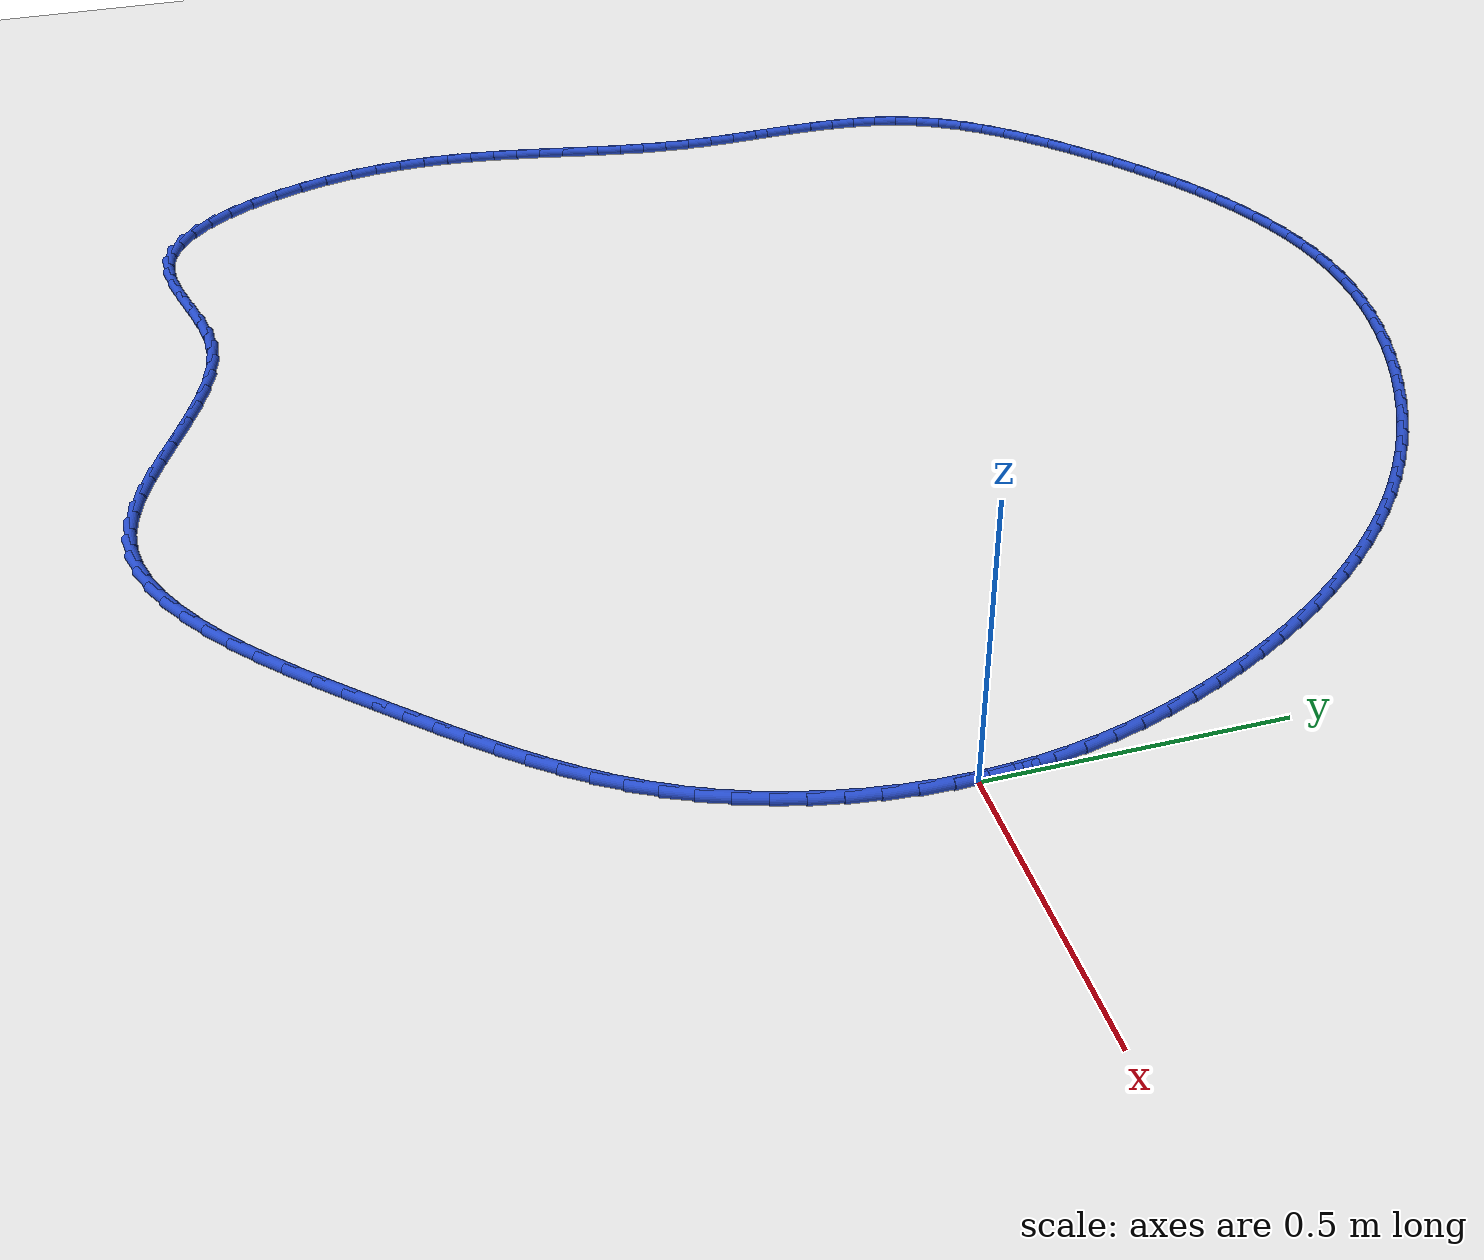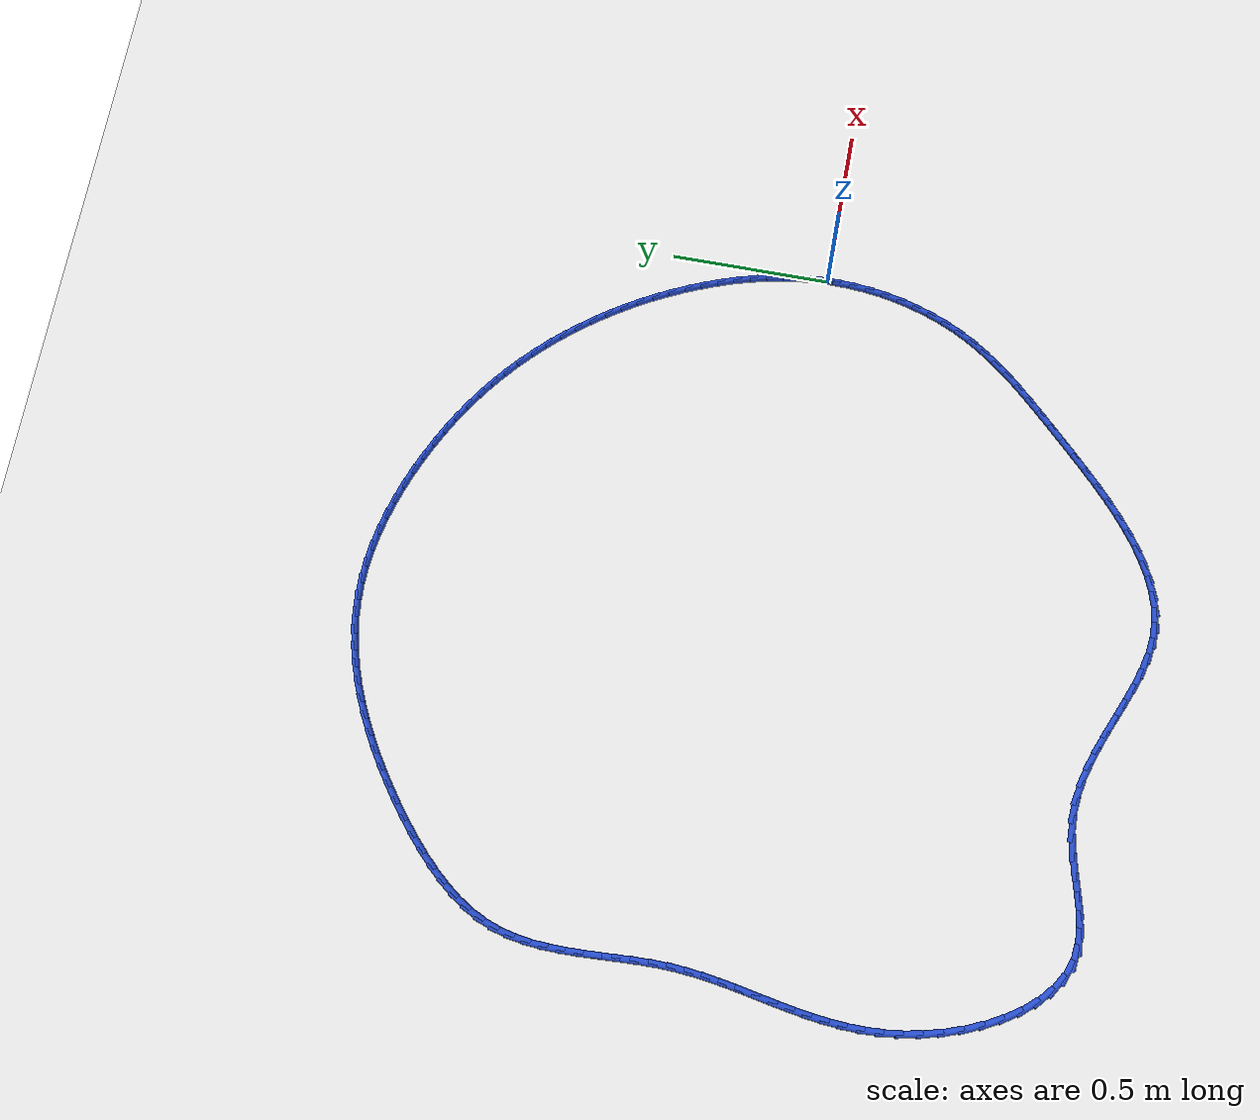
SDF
<sdf version="1.6">
 <world name="default">
  <light name="sun" type="directional">
   <pose>0 0 10 0 -0 0</pose>
   <diffuse>0.8 0.8 0.8 1</diffuse>
   <specular>0.2 0.2 0.2 1</specular>
   <attenuation>
    <range>1000</range>
    <constant>0.9</constant>
    <linear>0.01</linear>
    <quadratic>0.001</quadratic>
   </attenuation>
   <direction>-0.5 0.1 -0.9</direction>
  </light>
  <model name="ground_plane">
   <static>1</static>
   <link name="link">
    <collision name="collision">
     <geometry><plane><normal>0 0 1</normal><size>100 100</size></plane></geometry>
     <surface><friction><ode><mu>100</mu><mu2>50</mu2></ode></friction></surface>
    </collision>
    <visual name="visual">
     <cast_shadows>0</cast_shadows>
     <geometry><plane><normal>0 0 1</normal><size>100 100</size></plane></geometry>
     <material>
      <script><uri>file://media/materials/scripts/gazebo.material</uri><name>Gazebo/WhiteGlow</name></script>
     </material>
    </visual>
   </link>
  </model>
  <gravity>0 0 -9.8</gravity>
  <magnetic_field>6e-06 2.3e-05 -4.2e-05</magnetic_field>
  <atmosphere type="adiabatic"/>
  <physics name="default_physics" default="0" type="ode">
   <max_step_size>0.001</max_step_size>
   <real_time_factor>1</real_time_factor>
   <real_time_update_rate>1000</real_time_update_rate>
  </physics>
  <scene><ambient>0.4 0.4 0.4 1</ambient><background>0.7 0.7 0.7 1</background><shadows>1</shadows></scene>
  <spherical_coordinates>
   <surface_model>EARTH_WGS84</surface_model>
   <latitude_deg>0</latitude_deg>
   <longitude_deg>0</longitude_deg>
   <elevation>0</elevation>
   <heading_deg>0</heading_deg>
  </spherical_coordinates>
  <model name="line">
   <link name="link_0">
    <pose>-1.3877787807814457e-17 -5.551115123125783e-17 0.01 0 1.57 -1.5294799865286883</pose>
    <collision name="collision">
     <geometry><cylinder><radius>0.01</radius><length>0.08</length></cylinder></geometry>
    </collision>
    <visual name="visual">
     <material>
      <script><name>Gazebo/Blue</name><uri>file://media/materials/scripts/gazebo.material</uri></script>
     </material>
     <geometry><cylinder><radius>0.01</radius><length>0.08</length></cylinder></geometry>
    </visual>
   </link>
   <link name="link_1">
    <pose>-0.0021841628093463516 0.05283429839335736 0.01 0 1.57 -1.4750954064875892</pose>
    <collision name="collision">
     <geometry><cylinder><radius>0.01</radius><length>0.08</length></cylinder></geometry>
    </collision>
    <visual name="visual">
     <material>
      <script><name>Gazebo/Blue</name><uri>file://media/materials/scripts/gazebo.material</uri></script>
     </material>
     <geometry><cylinder><radius>0.01</radius><length>0.08</length></cylinder></geometry>
    </visual>
   </link>
   <link name="link_2">
    <pose>-0.0072178018318670885 0.10527122873435651 0.01 0 1.57 -1.4231612417951556</pose>
    <collision name="collision">
     <geometry><cylinder><radius>0.01</radius><length>0.08</length></cylinder></geometry>
    </collision>
    <visual name="visual">
     <material>
      <script><name>Gazebo/Blue</name><uri>file://media/materials/scripts/gazebo.material</uri></script>
     </material>
     <geometry><cylinder><radius>0.01</radius><length>0.08</length></cylinder></geometry>
    </visual>
   </link>
   <link name="link_3">
    <pose>-0.014951831685492925 0.1572761937106726 0.01 0 1.57 -1.3738176894232064</pose>
    <collision name="collision">
     <geometry><cylinder><radius>0.01</radius><length>0.08</length></cylinder></geometry>
    </collision>
    <visual name="visual">
     <material>
      <script><name>Gazebo/Blue</name><uri>file://media/materials/scripts/gazebo.material</uri></script>
     </material>
     <geometry><cylinder><radius>0.01</radius><length>0.08</length></cylinder></geometry>
    </visual>
   </link>
   <link name="link_4">
    <pose>-0.025237166988154536 0.20881459600998065 0.01 0 1.57 -1.3271413367178064</pose>
    <collision name="collision">
     <geometry><cylinder><radius>0.01</radius><length>0.08</length></cylinder></geometry>
    </collision>
    <visual name="visual">
     <material>
      <script><name>Gazebo/Blue</name><uri>file://media/materials/scripts/gazebo.material</uri></script>
     </material>
     <geometry><cylinder><radius>0.01</radius><length>0.08</length></cylinder></geometry>
    </visual>
   </link>
   <link name="link_5">
    <pose>-0.03792472235778264 0.25985183831995606 0.01 0 1.57 -1.283154380369551</pose>
    <collision name="collision">
     <geometry><cylinder><radius>0.01</radius><length>0.08</length></cylinder></geometry>
    </collision>
    <visual name="visual">
     <material>
      <script><name>Gazebo/Blue</name><uri>file://media/materials/scripts/gazebo.material</uri></script>
     </material>
     <geometry><cylinder><radius>0.01</radius><length>0.08</length></cylinder></geometry>
    </visual>
   </link>
   <link name="link_6">
    <pose>-0.052865412412307924 0.3103533233282738 0.01 0 1.57 -1.2418347899871558</pose>
    <collision name="collision">
     <geometry><cylinder><radius>0.01</radius><length>0.08</length></cylinder></geometry>
    </collision>
    <visual name="visual">
     <material>
      <script><name>Gazebo/Blue</name><uri>file://media/materials/scripts/gazebo.material</uri></script>
     </material>
     <geometry><cylinder><radius>0.01</radius><length>0.08</length></cylinder></geometry>
    </visual>
   </link>
   <link name="link_7">
    <pose>-0.06991015176966103 0.36028445372260887 0.01 0 1.57 -1.203126390044786</pose>
    <collision name="collision">
     <geometry><cylinder><radius>0.01</radius><length>0.08</length></cylinder></geometry>
    </collision>
    <visual name="visual">
     <material>
      <script><name>Gazebo/Blue</name><uri>file://media/materials/scripts/gazebo.material</uri></script>
     </material>
     <geometry><cylinder><radius>0.01</radius><length>0.08</length></cylinder></geometry>
    </visual>
   </link>
   <link name="link_8">
    <pose>-0.08890985504777274 0.4096106321906368 0.01 0 1.57 -1.166894859681101</pose>
    <collision name="collision">
     <geometry><cylinder><radius>0.01</radius><length>0.08</length></cylinder></geometry>
    </collision>
    <visual name="visual">
     <material>
      <script><name>Gazebo/Blue</name><uri>file://media/materials/scripts/gazebo.material</uri></script>
     </material>
     <geometry><cylinder><radius>0.01</radius><length>0.08</length></cylinder></geometry>
    </visual>
   </link>
   <link name="link_9">
    <pose>-0.10971800299744766 0.45829608380879305 0.01 0 1.57 -1.131835386523721</pose>
    <collision name="collision">
     <geometry><cylinder><radius>0.01</radius><length>0.08</length></cylinder></geometry>
    </collision>
    <visual name="visual">
     <material>
      <script><name>Gazebo/Blue</name><uri>file://media/materials/scripts/gazebo.material</uri></script>
     </material>
     <geometry><cylinder><radius>0.01</radius><length>0.08</length></cylinder></geometry>
    </visual>
   </link>
   <link name="link_10">
    <pose>-0.13224623940071267 0.5062783423469224 0.01 0 1.57 -1.096649820325048</pose>
    <collision name="collision">
     <geometry><cylinder><radius>0.01</radius><length>0.08</length></cylinder></geometry>
    </collision>
    <visual name="visual">
     <material>
      <script><name>Gazebo/Blue</name><uri>file://media/materials/scripts/gazebo.material</uri></script>
     </material>
     <geometry><cylinder><radius>0.01</radius><length>0.08</length></cylinder></geometry>
    </visual>
   </link>
   <link name="link_11">
    <pose>-0.15646389834648894 0.553468467203844 0.01 0 1.57 -1.061188693983388</pose>
    <collision name="collision">
     <geometry><cylinder><radius>0.01</radius><length>0.08</length></cylinder></geometry>
    </collision>
    <visual name="visual">
     <material>
      <script><name>Gazebo/Blue</name><uri>file://media/materials/scripts/gazebo.material</uri></script>
     </material>
     <geometry><cylinder><radius>0.01</radius><length>0.08</length></cylinder></geometry>
    </visual>
   </link>
   <link name="link_12">
    <pose>-0.18234278550973193 0.5997763835551553 0.01 0 1.57 -1.025355406005655</pose>
    <collision name="collision">
     <geometry><cylinder><radius>0.01</radius><length>0.08</length></cylinder></geometry>
    </collision>
    <visual name="visual">
     <material>
      <script><name>Gazebo/Blue</name><uri>file://media/materials/scripts/gazebo.material</uri></script>
     </material>
     <geometry><cylinder><radius>0.01</radius><length>0.08</length></cylinder></geometry>
    </visual>
   </link>
   <link name="link_13">
    <pose>-0.20985470656539704 0.6451120165764535 0.01 0 1.57 -0.9890550751553886</pose>
    <collision name="collision">
     <geometry><cylinder><radius>0.01</radius><length>0.08</length></cylinder></geometry>
    </collision>
    <visual name="visual">
     <material>
      <script><name>Gazebo/Blue</name><uri>file://media/materials/scripts/gazebo.material</uri></script>
     </material>
     <geometry><cylinder><radius>0.01</radius><length>0.08</length></cylinder></geometry>
    </visual>
   </link>
   <link name="link_14">
    <pose>-0.23897146718843976 0.6893852914433367 0.01 0 1.57 -0.9521948671829819</pose>
    <collision name="collision">
     <geometry><cylinder><radius>0.01</radius><length>0.08</length></cylinder></geometry>
    </collision>
    <visual name="visual">
     <material>
      <script><name>Gazebo/Blue</name><uri>file://media/materials/scripts/gazebo.material</uri></script>
     </material>
     <geometry><cylinder><radius>0.01</radius><length>0.08</length></cylinder></geometry>
    </visual>
   </link>
   <link name="link_15">
    <pose>-0.2696648730538156 0.7325061333314024 0.01 0 1.57 -0.9146844777312849</pose>
    <collision name="collision">
     <geometry><cylinder><radius>0.01</radius><length>0.08</length></cylinder></geometry>
    </collision>
    <visual name="visual">
     <material>
      <script><name>Gazebo/Blue</name><uri>file://media/materials/scripts/gazebo.material</uri></script>
     </material>
     <geometry><cylinder><radius>0.01</radius><length>0.08</length></cylinder></geometry>
    </visual>
   </link>
   <link name="link_16">
    <pose>-0.30190672983648004 0.774384467416248 0.01 0 1.57 -0.8764368001293903</pose>
    <collision name="collision">
     <geometry><cylinder><radius>0.01</radius><length>0.08</length></cylinder></geometry>
    </collision>
    <visual name="visual">
     <material>
      <script><name>Gazebo/Blue</name><uri>file://media/materials/scripts/gazebo.material</uri></script>
     </material>
     <geometry><cylinder><radius>0.01</radius><length>0.08</length></cylinder></geometry>
    </visual>
   </link>
   <link name="link_17">
    <pose>-0.3356688432113885 0.8149302188734715 0.01 0 1.57 -0.8373688058446191</pose>
    <collision name="collision">
     <geometry><cylinder><radius>0.01</radius><length>0.08</length></cylinder></geometry>
    </collision>
    <visual name="visual">
     <material>
      <script><name>Gazebo/Blue</name><uri>file://media/materials/scripts/gazebo.material</uri></script>
     </material>
     <geometry><cylinder><radius>0.01</radius><length>0.08</length></cylinder></geometry>
    </visual>
   </link>
   <link name="link_18">
    <pose>-0.37092301885349654 0.8540533128786704 0.01 0 1.57 -0.7974026625784103</pose>
    <collision name="collision">
     <geometry><cylinder><radius>0.01</radius><length>0.08</length></cylinder></geometry>
    </collision>
    <visual name="visual">
     <material>
      <script><name>Gazebo/Blue</name><uri>file://media/materials/scripts/gazebo.material</uri></script>
     </material>
     <geometry><cylinder><radius>0.01</radius><length>0.08</length></cylinder></geometry>
    </visual>
   </link>
   <link name="link_19">
    <pose>-0.4076410624377597 0.8916636746074424 0.01 0 1.57 -0.7564671094453537</pose>
    <collision name="collision">
     <geometry><cylinder><radius>0.01</radius><length>0.08</length></cylinder></geometry>
    </collision>
    <visual name="visual">
     <material>
      <script><name>Gazebo/Blue</name><uri>file://media/materials/scripts/gazebo.material</uri></script>
     </material>
     <geometry><cylinder><radius>0.01</radius><length>0.08</length></cylinder></geometry>
    </visual>
   </link>
   <link name="link_20">
    <pose>-0.4457947796391332 0.9276712292353846 0.01 0 1.57 -0.7145105895369924</pose>
    <collision name="collision">
     <geometry><cylinder><radius>0.01</radius><length>0.08</length></cylinder></geometry>
    </collision>
    <visual name="visual">
     <material>
      <script><name>Gazebo/Blue</name><uri>file://media/materials/scripts/gazebo.material</uri></script>
     </material>
     <geometry><cylinder><radius>0.01</radius><length>0.08</length></cylinder></geometry>
    </visual>
   </link>
   <link name="link_21">
    <pose>-0.48535586840915845 0.9619866050661755 0.01 0 1.57 -0.6720824993852983</pose>
    <collision name="collision">
     <geometry><cylinder><radius>0.01</radius><length>0.08</length></cylinder></geometry>
    </collision>
    <visual name="visual">
     <material>
      <script><name>Gazebo/Blue</name><uri>file://media/materials/scripts/gazebo.material</uri></script>
     </material>
     <geometry><cylinder><radius>0.01</radius><length>0.08</length></cylinder></geometry>
    </visual>
   </link>
   <link name="link_22">
    <pose>-0.526290538794819 0.9945562508405971 0.01 0 1.57 -0.6300833568327313</pose>
    <collision name="collision">
     <geometry><cylinder><radius>0.01</radius><length>0.08</length></cylinder></geometry>
    </collision>
    <visual name="visual">
     <material>
      <script><name>Gazebo/Blue</name><uri>file://media/materials/scripts/gazebo.material</uri></script>
     </material>
     <geometry><cylinder><radius>0.01</radius><length>0.08</length></cylinder></geometry>
    </visual>
   </link>
   <link name="link_23">
    <pose>-0.5685570125882284 1.025378755925824 0.01 0 1.57 -0.5886511421573137</pose>
    <collision name="collision">
     <geometry><cylinder><radius>0.01</radius><length>0.08</length></cylinder></geometry>
    </collision>
    <visual name="visual">
     <material>
      <script><name>Gazebo/Blue</name><uri>file://media/materials/scripts/gazebo.material</uri></script>
     </material>
     <geometry><cylinder><radius>0.01</radius><length>0.08</length></cylinder></geometry>
    </visual>
   </link>
   <link name="link_24">
    <pose>-0.6121128815877744 1.054456821759565 0.01 0 1.57 -0.5478471391222542</pose>
    <collision name="collision">
     <geometry><cylinder><radius>0.01</radius><length>0.08</length></cylinder></geometry>
    </collision>
    <visual name="visual">
     <material>
      <script><name>Gazebo/Blue</name><uri>file://media/materials/scripts/gazebo.material</uri></script>
     </material>
     <geometry><cylinder><radius>0.01</radius><length>0.08</length></cylinder></geometry>
    </visual>
   </link>
   <link name="link_25">
    <pose>-0.6569157375918444 1.0817931497795288 0.01 0 1.57 -0.5077228907239659</pose>
    <collision name="collision">
     <geometry><cylinder><radius>0.01</radius><length>0.08</length></cylinder></geometry>
    </collision>
    <visual name="visual">
     <material>
      <script><name>Gazebo/Blue</name><uri>file://media/materials/scripts/gazebo.material</uri></script>
     </material>
     <geometry><cylinder><radius>0.01</radius><length>0.08</length></cylinder></geometry>
    </visual>
   </link>
   <link name="link_26">
    <pose>-0.7029231723988265 1.1073904414234244 0.01 0 1.57 -0.468320224909798</pose>
    <collision name="collision">
     <geometry><cylinder><radius>0.01</radius><length>0.08</length></cylinder></geometry>
    </collision>
    <visual name="visual">
     <material>
      <script><name>Gazebo/Blue</name><uri>file://media/materials/scripts/gazebo.material</uri></script>
     </material>
     <geometry><cylinder><radius>0.01</radius><length>0.08</length></cylinder></geometry>
    </visual>
   </link>
   <link name="link_27">
    <pose>-0.750092777807108 1.1312513981289607 0.01 0 1.57 -0.4296699337620087</pose>
    <collision name="collision">
     <geometry><cylinder><radius>0.01</radius><length>0.08</length></cylinder></geometry>
    </collision>
    <visual name="visual">
     <material>
      <script><name>Gazebo/Blue</name><uri>file://media/materials/scripts/gazebo.material</uri></script>
     </material>
     <geometry><cylinder><radius>0.01</radius><length>0.08</length></cylinder></geometry>
    </visual>
   </link>
   <link name="link_28">
    <pose>-0.7983820795866092 1.1533785989535899 0.01 0 1.57 -0.39098116729048515</pose>
    <collision name="collision">
     <geometry><cylinder><radius>0.01</radius><length>0.08</length></cylinder></geometry>
    </collision>
    <visual name="visual">
     <material>
      <script><name>Gazebo/Blue</name><uri>file://media/materials/scripts/gazebo.material</uri></script>
     </material>
     <geometry><cylinder><radius>0.01</radius><length>0.08</length></cylinder></geometry>
    </visual>
   </link>
   <link name="link_29">
    <pose>-0.847715973489055 1.1737141449499853 0.01 0 1.57 -0.34994606891573365</pose>
    <collision name="collision">
     <geometry><cylinder><radius>0.01</radius><length>0.08</length></cylinder></geometry>
    </collision>
    <visual name="visual">
     <material>
      <script><name>Gazebo/Blue</name><uri>file://media/materials/scripts/gazebo.material</uri></script>
     </material>
     <geometry><cylinder><radius>0.01</radius><length>0.08</length></cylinder></geometry>
    </visual>
   </link>
   <link name="link_30">
    <pose>-0.8979341012687312 1.1920421234169236 0.01 0 1.57 -0.3058147048853022</pose>
    <collision name="collision">
     <geometry><cylinder><radius>0.01</radius><length>0.08</length></cylinder></geometry>
    </collision>
    <visual name="visual">
     <material>
      <script><name>Gazebo/Blue</name><uri>file://media/materials/scripts/gazebo.material</uri></script>
     </material>
     <geometry><cylinder><radius>0.01</radius><length>0.08</length></cylinder></geometry>
    </visual>
   </link>
   <link name="link_31">
    <pose>-0.9488623542239586 1.2081211359137454 0.01 0 1.57 -0.2581489164474256</pose>
    <collision name="collision">
     <geometry><cylinder><radius>0.01</radius><length>0.08</length></cylinder></geometry>
    </collision>
    <visual name="visual">
     <material>
      <script><name>Gazebo/Blue</name><uri>file://media/materials/scripts/gazebo.material</uri></script>
     </material>
     <geometry><cylinder><radius>0.01</radius><length>0.08</length></cylinder></geometry>
    </visual>
   </link>
   <link name="link_32">
    <pose>-1.0003266236530575 1.2217097839997877 0.01 0 1.57 -0.2065003464584691</pose>
    <collision name="collision">
     <geometry><cylinder><radius>0.01</radius><length>0.08</length></cylinder></geometry>
    </collision>
    <visual name="visual">
     <material>
      <script><name>Gazebo/Blue</name><uri>file://media/materials/scripts/gazebo.material</uri></script>
     </material>
     <geometry><cylinder><radius>0.01</radius><length>0.08</length></cylinder></geometry>
    </visual>
   </link>
   <link name="link_33">
    <pose>-1.0521528008543484 1.2325666692343904 0.01 0 1.57 -0.1504243978866744</pose>
    <collision name="collision">
     <geometry><cylinder><radius>0.01</radius><length>0.08</length></cylinder></geometry>
    </collision>
    <visual name="visual">
     <material>
      <script><name>Gazebo/Blue</name><uri>file://media/materials/scripts/gazebo.material</uri></script>
     </material>
     <geometry><cylinder><radius>0.01</radius><length>0.08</length></cylinder></geometry>
    </visual>
   </link>
   <link name="link_34">
    <pose>-1.1041667771261514 1.2404503931768915 0.01 0 1.57 -0.08950409748120725</pose>
    <collision name="collision">
     <geometry><cylinder><radius>0.01</radius><length>0.08</length></cylinder></geometry>
    </collision>
    <visual name="visual">
     <material>
      <script><name>Gazebo/Blue</name><uri>file://media/materials/scripts/gazebo.material</uri></script>
     </material>
     <geometry><cylinder><radius>0.01</radius><length>0.08</length></cylinder></geometry>
    </visual>
   </link>
   <link name="link_35">
    <pose>-1.156194443766787 1.2451195573866296 0.01 0 1.57 -0.023386335153758573</pose>
    <collision name="collision">
     <geometry><cylinder><radius>0.01</radius><length>0.08</length></cylinder></geometry>
    </collision>
    <visual name="visual">
     <material>
      <script><name>Gazebo/Blue</name><uri>file://media/materials/scripts/gazebo.material</uri></script>
     </material>
     <geometry><cylinder><radius>0.01</radius><length>0.08</length></cylinder></geometry>
    </visual>
   </link>
   <link name="link_36">
    <pose>-1.2080616920745755 1.2463327634229437 0.01 0 1.57 0.04794509406988395</pose>
    <collision name="collision">
     <geometry><cylinder><radius>0.01</radius><length>0.08</length></cylinder></geometry>
    </collision>
    <visual name="visual">
     <material>
      <script><name>Gazebo/Blue</name><uri>file://media/materials/scripts/gazebo.material</uri></script>
     </material>
     <geometry><cylinder><radius>0.01</radius><length>0.08</length></cylinder></geometry>
    </visual>
   </link>
   <link name="link_37">
    <pose>-1.2595979207297625 1.243859959030062 0.01 0 1.57 0.12009842457078553</pose>
    <collision name="collision">
     <geometry><cylinder><radius>0.01</radius><length>0.08</length></cylinder></geometry>
    </collision>
    <visual name="visual">
     <material>
      <script><name>Gazebo/Blue</name><uri>file://media/materials/scripts/gazebo.material</uri></script>
     </material>
     <geometry><cylinder><radius>0.01</radius><length>0.08</length></cylinder></geometry>
    </visual>
   </link>
   <link name="link_38">
    <pose>-1.310701085496671 1.2376928702951726 0.01 0 1.57 0.18867450825872953</pose>
    <collision name="collision">
     <geometry><cylinder><radius>0.01</radius><length>0.08</length></cylinder></geometry>
    </collision>
    <visual name="visual">
     <material>
      <script><name>Gazebo/Blue</name><uri>file://media/materials/scripts/gazebo.material</uri></script>
     </material>
     <geometry><cylinder><radius>0.01</radius><length>0.08</length></cylinder></geometry>
    </visual>
   </link>
   <link name="link_39">
    <pose>-1.3613315771763312 1.2280251971666563 0.01 0 1.57 0.253168925779506</pose>
    <collision name="collision">
     <geometry><cylinder><radius>0.01</radius><length>0.08</length></cylinder></geometry>
    </collision>
    <visual name="visual">
     <material>
      <script><name>Gazebo/Blue</name><uri>file://media/materials/scripts/gazebo.material</uri></script>
     </material>
     <geometry><cylinder><radius>0.01</radius><length>0.08</length></cylinder></geometry>
    </visual>
   </link>
   <link name="link_40">
    <pose>-1.411452066182845 1.2150580140140304 0.01 0 1.57 0.31339865597737976</pose>
    <collision name="collision">
     <geometry><cylinder><radius>0.01</radius><length>0.08</length></cylinder></geometry>
    </collision>
    <visual name="visual">
     <material>
      <script><name>Gazebo/Blue</name><uri>file://media/materials/scripts/gazebo.material</uri></script>
     </material>
     <geometry><cylinder><radius>0.01</radius><length>0.08</length></cylinder></geometry>
    </visual>
   </link>
   <link name="link_41">
    <pose>-1.4610252229303158 1.1989923952068111 0.01 0 1.57 0.3693281852339817</pose>
    <collision name="collision">
     <geometry><cylinder><radius>0.01</radius><length>0.08</length></cylinder></geometry>
    </collision>
    <visual name="visual">
     <material>
      <script><name>Gazebo/Blue</name><uri>file://media/materials/scripts/gazebo.material</uri></script>
     </material>
     <geometry><cylinder><radius>0.01</radius><length>0.08</length></cylinder></geometry>
    </visual>
   </link>
   <link name="link_42">
    <pose>-1.510013717832845 1.1800294151145159 0.01 0 1.57 0.4210357594181196</pose>
    <collision name="collision">
     <geometry><cylinder><radius>0.01</radius><length>0.08</length></cylinder></geometry>
    </collision>
    <visual name="visual">
     <material>
      <script><name>Gazebo/Blue</name><uri>file://media/materials/scripts/gazebo.material</uri></script>
     </material>
     <geometry><cylinder><radius>0.01</radius><length>0.08</length></cylinder></geometry>
    </visual>
   </link>
   <link name="link_43">
    <pose>-1.5583802213045352 1.1583701481066606 0.01 0 1.57 0.4686804549283859</pose>
    <collision name="collision">
     <geometry><cylinder><radius>0.01</radius><length>0.08</length></cylinder></geometry>
    </collision>
    <visual name="visual">
     <material>
      <script><name>Gazebo/Blue</name><uri>file://media/materials/scripts/gazebo.material</uri></script>
     </material>
     <geometry><cylinder><radius>0.01</radius><length>0.08</length></cylinder></geometry>
    </visual>
   </link>
   <link name="link_44">
    <pose>-1.6060874037594892 1.1342156685527627 0.01 0 1.57 0.5124733792224611</pose>
    <collision name="collision">
     <geometry><cylinder><radius>0.01</radius><length>0.08</length></cylinder></geometry>
    </collision>
    <visual name="visual">
     <material>
      <script><name>Gazebo/Blue</name><uri>file://media/materials/scripts/gazebo.material</uri></script>
     </material>
     <geometry><cylinder><radius>0.01</radius><length>0.08</length></cylinder></geometry>
    </visual>
   </link>
   <link name="link_45">
    <pose>-1.6530979356118094 1.1077670508223385 0.01 0 1.57 0.5526544014861036</pose>
    <collision name="collision">
     <geometry><cylinder><radius>0.01</radius><length>0.08</length></cylinder></geometry>
    </collision>
    <visual name="visual">
     <material>
      <script><name>Gazebo/Blue</name><uri>file://media/materials/scripts/gazebo.material</uri></script>
     </material>
     <geometry><cylinder><radius>0.01</radius><length>0.08</length></cylinder></geometry>
    </visual>
   </link>
   <link name="link_46">
    <pose>-1.6993744872755978 1.0792253692849045 0.01 0 1.57 0.5894745075956613</pose>
    <collision name="collision">
     <geometry><cylinder><radius>0.01</radius><length>0.08</length></cylinder></geometry>
    </collision>
    <visual name="visual">
     <material>
      <script><name>Gazebo/Blue</name><uri>file://media/materials/scripts/gazebo.material</uri></script>
     </material>
     <geometry><cylinder><radius>0.01</radius><length>0.08</length></cylinder></geometry>
    </visual>
   </link>
   <link name="link_47">
    <pose>-1.7448797291649565 1.0487916983099779 0.01 0 1.57 0.6231831463204608</pose>
    <collision name="collision">
     <geometry><cylinder><radius>0.01</radius><length>0.08</length></cylinder></geometry>
    </collision>
    <visual name="visual">
     <material>
      <script><name>Gazebo/Blue</name><uri>file://media/materials/scripts/gazebo.material</uri></script>
     </material>
     <geometry><cylinder><radius>0.01</radius><length>0.08</length></cylinder></geometry>
    </visual>
   </link>
   <link name="link_48">
    <pose>-1.789576331693989 1.016667112267075 0.01 0 1.57 0.6540196357630114</pose>
    <collision name="collision">
     <geometry><cylinder><radius>0.01</radius><length>0.08</length></cylinder></geometry>
    </collision>
    <visual name="visual">
     <material>
      <script><name>Gazebo/Blue</name><uri>file://media/materials/scripts/gazebo.material</uri></script>
     </material>
     <geometry><cylinder><radius>0.01</radius><length>0.08</length></cylinder></geometry>
    </visual>
   </link>
   <link name="link_49">
    <pose>-1.8334269652767965 0.9830526855257128 0.01 0 1.57 0.6827512179668036</pose>
    <collision name="collision">
     <geometry><cylinder><radius>0.01</radius><length>0.08</length></cylinder></geometry>
    </collision>
    <visual name="visual">
     <material>
      <script><name>Gazebo/Blue</name><uri>file://media/materials/scripts/gazebo.material</uri></script>
     </material>
     <geometry><cylinder><radius>0.01</radius><length>0.08</length></cylinder></geometry>
    </visual>
   </link>
   <link name="link_50">
    <pose>-1.8763650993271739 0.9481344561324505 0.01 0 1.57 0.715752641495144</pose>
    <collision name="collision">
     <geometry><cylinder><radius>0.01</radius><length>0.08</length></cylinder></geometry>
    </collision>
    <visual name="visual">
     <material>
      <script><name>Gazebo/Blue</name><uri>file://media/materials/scripts/gazebo.material</uri></script>
     </material>
     <geometry><cylinder><radius>0.01</radius><length>0.08</length></cylinder></geometry>
    </visual>
   </link>
   <link name="link_51">
    <pose>-1.9179985634133236 0.9119307820600733 0.01 0 1.57 0.7575008575013443</pose>
    <collision name="collision">
     <geometry><cylinder><radius>0.01</radius><length>0.08</length></cylinder></geometry>
    </collision>
    <visual name="visual">
     <material>
      <script><name>Gazebo/Blue</name><uri>file://media/materials/scripts/gazebo.material</uri></script>
     </material>
     <geometry><cylinder><radius>0.01</radius><length>0.08</length></cylinder></geometry>
    </visual>
   </link>
   <link name="link_52">
    <pose>-1.9577314790560656 0.8743551269299016 0.01 0 1.57 0.8090259919191154</pose>
    <collision name="collision">
     <geometry><cylinder><radius>0.01</radius><length>0.08</length></cylinder></geometry>
    </collision>
    <visual name="visual">
     <material>
      <script><name>Gazebo/Blue</name><uri>file://media/materials/scripts/gazebo.material</uri></script>
     </material>
     <geometry><cylinder><radius>0.01</radius><length>0.08</length></cylinder></geometry>
    </visual>
   </link>
   <link name="link_53">
    <pose>-1.9949648481953908 0.8353193480133265 0.01 0 1.57 0.8714979208902035</pose>
    <collision name="collision">
     <geometry><cylinder><radius>0.01</radius><length>0.08</length></cylinder></geometry>
    </collision>
    <visual name="visual">
     <material>
      <script><name>Gazebo/Blue</name><uri>file://media/materials/scripts/gazebo.material</uri></script>
     </material>
     <geometry><cylinder><radius>0.01</radius><length>0.08</length></cylinder></geometry>
    </visual>
   </link>
   <link name="link_54">
    <pose>-2.0290996727712893 0.7947353025817376 0.01 0 1.57 0.9461721293149064</pose>
    <collision name="collision">
     <geometry><cylinder><radius>0.01</radius><length>0.08</length></cylinder></geometry>
    </collision>
    <visual name="visual">
     <material>
      <script><name>Gazebo/Blue</name><uri>file://media/materials/scripts/gazebo.material</uri></script>
     </material>
     <geometry><cylinder><radius>0.01</radius><length>0.08</length></cylinder></geometry>
    </visual>
   </link>
   <link name="link_55">
    <pose>-2.059536954723751 0.7525148479065245 0.01 0 1.57 1.0341712876203266</pose>
    <collision name="collision">
     <geometry><cylinder><radius>0.01</radius><length>0.08</length></cylinder></geometry>
    </collision>
    <visual name="visual">
     <material>
      <script><name>Gazebo/Blue</name><uri>file://media/materials/scripts/gazebo.material</uri></script>
     </material>
     <geometry><cylinder><radius>0.01</radius><length>0.08</length></cylinder></geometry>
    </visual>
   </link>
   <link name="link_56">
    <pose>-2.0856776959927656 0.7085698412590772 0.01 0 1.57 1.1361161250300202</pose>
    <collision name="collision">
     <geometry><cylinder><radius>0.01</radius><length>0.08</length></cylinder></geometry>
    </collision>
    <visual name="visual">
     <material>
      <script><name>Gazebo/Blue</name><uri>file://media/materials/scripts/gazebo.material</uri></script>
     </material>
     <geometry><cylinder><radius>0.01</radius><length>0.08</length></cylinder></geometry>
    </visual>
   </link>
   <link name="link_57">
    <pose>-2.106922898518324 0.6628121399107856 0.01 0 1.57 1.2499806652376269</pose>
    <collision name="collision">
     <geometry><cylinder><radius>0.01</radius><length>0.08</length></cylinder></geometry>
    </collision>
    <visual name="visual">
     <material>
      <script><name>Gazebo/Blue</name><uri>file://media/materials/scripts/gazebo.material</uri></script>
     </material>
     <geometry><cylinder><radius>0.01</radius><length>0.08</length></cylinder></geometry>
    </visual>
   </link>
   <link name="link_58">
    <pose>-2.1227528856844984 0.6151737687110339 0.01 0 1.57 1.356681667277702</pose>
    <collision name="collision">
     <geometry><cylinder><radius>0.01</radius><length>0.08</length></cylinder></geometry>
    </collision>
    <visual name="visual">
     <material>
      <script><name>Gazebo/Blue</name><uri>file://media/materials/scripts/gazebo.material</uri></script>
     </material>
     <geometry><cylinder><radius>0.01</radius><length>0.08</length></cylinder></geometry>
    </visual>
   </link>
   <link name="link_59">
    <pose>-2.1334889790903238 0.5658005773744647 0.01 0 1.57 1.4442001895601004</pose>
    <collision name="collision">
     <geometry><cylinder><radius>0.01</radius><length>0.08</length></cylinder></geometry>
    </collision>
    <visual name="visual">
     <material>
      <script><name>Gazebo/Blue</name><uri>file://media/materials/scripts/gazebo.material</uri></script>
     </material>
     <geometry><cylinder><radius>0.01</radius><length>0.08</length></cylinder></geometry>
    </visual>
   </link>
   <link name="link_60">
    <pose>-2.1399588930566726 0.5149671666089919 0.01 0 1.57 1.5124511974653672</pose>
    <collision name="collision">
     <geometry><cylinder><radius>0.01</radius><length>0.08</length></cylinder></geometry>
    </collision>
    <visual name="visual">
     <material>
      <script><name>Gazebo/Blue</name><uri>file://media/materials/scripts/gazebo.material</uri></script>
     </material>
     <geometry><cylinder><radius>0.01</radius><length>0.08</length></cylinder></geometry>
    </visual>
   </link>
   <link name="link_61">
    <pose>-2.1429972954216017 0.4629499050631125 0.01 0 1.57 1.5624533793194062</pose>
    <collision name="collision">
     <geometry><cylinder><radius>0.01</radius><length>0.08</length></cylinder></geometry>
    </collision>
    <visual name="visual">
     <material>
      <script><name>Gazebo/Blue</name><uri>file://media/materials/scripts/gazebo.material</uri></script>
     </material>
     <geometry><cylinder><radius>0.01</radius><length>0.08</length></cylinder></geometry>
    </visual>
   </link>
   <link name="link_62">
    <pose>-2.143438854023169 0.41002516138532413 0.01 0 1.57 -1.5461426320589489</pose>
    <collision name="collision">
     <geometry><cylinder><radius>0.01</radius><length>0.08</length></cylinder></geometry>
    </collision>
    <visual name="visual">
     <material>
      <script><name>Gazebo/Blue</name><uri>file://media/materials/scripts/gazebo.material</uri></script>
     </material>
     <geometry><cylinder><radius>0.01</radius><length>0.08</length></cylinder></geometry>
    </visual>
   </link>
   <link name="link_63">
    <pose>-2.1421182366994294 0.35646930422412326 0.01 0 1.57 -1.529119485078104</pose>
    <collision name="collision">
     <geometry><cylinder><radius>0.01</radius><length>0.08</length></cylinder></geometry>
    </collision>
    <visual name="visual">
     <material>
      <script><name>Gazebo/Blue</name><uri>file://media/materials/scripts/gazebo.material</uri></script>
     </material>
     <geometry><cylinder><radius>0.01</radius><length>0.08</length></cylinder></geometry>
    </visual>
   </link>
   <link name="link_64">
    <pose>-2.1398701112884395 0.30255870222800757 0.01 0 1.57 -1.527463403814393</pose>
    <collision name="collision">
     <geometry><cylinder><radius>0.01</radius><length>0.08</length></cylinder></geometry>
    </collision>
    <visual name="visual">
     <material>
      <script><name>Gazebo/Blue</name><uri>file://media/materials/scripts/gazebo.material</uri></script>
     </material>
     <geometry><cylinder><radius>0.01</radius><length>0.08</length></cylinder></geometry>
    </visual>
   </link>
   <link name="link_65">
    <pose>-2.1375291456282564 0.2485697240454738 0.01 0 1.57 -1.5410763431459489</pose>
    <collision name="collision">
     <geometry><cylinder><radius>0.01</radius><length>0.08</length></cylinder></geometry>
    </collision>
    <visual name="visual">
     <material>
      <script><name>Gazebo/Blue</name><uri>file://media/materials/scripts/gazebo.material</uri></script>
     </material>
     <geometry><cylinder><radius>0.01</radius><length>0.08</length></cylinder></geometry>
    </visual>
   </link>
   <link name="link_66">
    <pose>-2.1359300075569356 0.19477873832501866 0.01 0 1.57 -1.570371644189685</pose>
    <collision name="collision">
     <geometry><cylinder><radius>0.01</radius><length>0.08</length></cylinder></geometry>
    </collision>
    <visual name="visual">
     <material>
      <script><name>Gazebo/Blue</name><uri>file://media/materials/scripts/gazebo.material</uri></script>
     </material>
     <geometry><cylinder><radius>0.01</radius><length>0.08</length></cylinder></geometry>
    </visual>
   </link>
   <link name="link_67">
    <pose>-2.135907364912534 0.14146211371514006 0.01 0 1.57 1.5259237822704175</pose>
    <collision name="collision">
     <geometry><cylinder><radius>0.01</radius><length>0.08</length></cylinder></geometry>
    </collision>
    <visual name="visual">
     <material>
      <script><name>Gazebo/Blue</name><uri>file://media/materials/scripts/gazebo.material</uri></script>
     </material>
     <geometry><cylinder><radius>0.01</radius><length>0.08</length></cylinder></geometry>
    </visual>
   </link>
   <link name="link_68">
    <pose>-2.1382681311447023 0.08888694684601181 0.01 0 1.57 1.476589265037115</pose>
    <collision name="collision">
     <geometry><cylinder><radius>0.01</radius><length>0.08</length></cylinder></geometry>
    </collision>
    <visual name="visual">
     <material>
      <script><name>Gazebo/Blue</name><uri>file://media/materials/scripts/gazebo.material</uri></script>
     </material>
     <geometry><cylinder><radius>0.01</radius><length>0.08</length></cylinder></geometry>
    </visual>
   </link>
   <link name="link_69">
    <pose>-2.1431612615686846 0.037100527671166 0.01 0 1.57 1.436666405462536</pose>
    <collision name="collision">
     <geometry><cylinder><radius>0.01</radius><length>0.08</length></cylinder></geometry>
    </collision>
    <visual name="visual">
     <material>
      <script><name>Gazebo/Blue</name><uri>file://media/materials/scripts/gazebo.material</uri></script>
     </material>
     <geometry><cylinder><radius>0.01</radius><length>0.08</length></cylinder></geometry>
    </visual>
   </link>
   <link name="link_70">
    <pose>-2.1500666725365467 -0.014073362348809815 0.01 0 1.57 1.4073793517712097</pose>
    <collision name="collision">
     <geometry><cylinder><radius>0.01</radius><length>0.08</length></cylinder></geometry>
    </collision>
    <visual name="visual">
     <material>
      <script><name>Gazebo/Blue</name><uri>file://media/materials/scripts/gazebo.material</uri></script>
     </material>
     <geometry><cylinder><radius>0.01</radius><length>0.08</length></cylinder></geometry>
    </visual>
   </link>
   <link name="link_71">
    <pose>-2.158434309652418 -0.06482095419964486 0.01 0 1.57 1.3890916363929153</pose>
    <collision name="collision">
     <geometry><cylinder><radius>0.01</radius><length>0.08</length></cylinder></geometry>
    </collision>
    <visual name="visual">
     <material>
      <script><name>Gazebo/Blue</name><uri>file://media/materials/scripts/gazebo.material</uri></script>
     </material>
     <geometry><cylinder><radius>0.01</radius><length>0.08</length></cylinder></geometry>
    </visual>
   </link>
   <link name="link_72">
    <pose>-2.167714118520429 -0.11532847886706946 0.01 0 1.57 1.3819685928390033</pose>
    <collision name="collision">
     <geometry><cylinder><radius>0.01</radius><length>0.08</length></cylinder></geometry>
    </collision>
    <visual name="visual">
     <material>
      <script><name>Gazebo/Blue</name><uri>file://media/materials/scripts/gazebo.material</uri></script>
     </material>
     <geometry><cylinder><radius>0.01</radius><length>0.08</length></cylinder></geometry>
    </visual>
   </link>
   <link name="link_73">
    <pose>-2.177356044744708 -0.16578216733681433 0.01 0 1.57 1.3860385637002255</pose>
    <collision name="collision">
     <geometry><cylinder><radius>0.01</radius><length>0.08</length></cylinder></geometry>
    </collision>
    <visual name="visual">
     <material>
      <script><name>Gazebo/Blue</name><uri>file://media/materials/scripts/gazebo.material</uri></script>
     </material>
     <geometry><cylinder><radius>0.01</radius><length>0.08</length></cylinder></geometry>
    </visual>
   </link>
   <link name="link_74">
    <pose>-2.186810033929385 -0.21636825059460796 0.01 0 1.57 1.4012188929763683</pose>
    <collision name="collision">
     <geometry><cylinder><radius>0.01</radius><length>0.08</length></cylinder></geometry>
    </collision>
    <visual name="visual">
     <material>
      <script><name>Gazebo/Blue</name><uri>file://media/materials/scripts/gazebo.material</uri></script>
     </material>
     <geometry><cylinder><radius>0.01</radius><length>0.08</length></cylinder></geometry>
    </visual>
   </link>
   <link name="link_75">
    <pose>-2.195526031678589 -0.26727295962618103 0.01 0 1.57 1.42730355954507</pose>
    <collision name="collision">
     <geometry><cylinder><radius>0.01</radius><length>0.08</length></cylinder></geometry>
    </collision>
    <visual name="visual">
     <material>
      <script><name>Gazebo/Blue</name><uri>file://media/materials/scripts/gazebo.material</uri></script>
     </material>
     <geometry><cylinder><radius>0.01</radius><length>0.08</length></cylinder></geometry>
    </visual>
   </link>
   <link name="link_76">
    <pose>-2.2029539835964513 -0.3186825254172635 0.01 0 1.57 1.4639157039639852</pose>
    <collision name="collision">
     <geometry><cylinder><radius>0.01</radius><length>0.08</length></cylinder></geometry>
    </collision>
    <visual name="visual">
     <material>
      <script><name>Gazebo/Blue</name><uri>file://media/materials/scripts/gazebo.material</uri></script>
     </material>
     <geometry><cylinder><radius>0.01</radius><length>0.08</length></cylinder></geometry>
    </visual>
   </link>
   <link name="link_77">
    <pose>-2.208543835287099 -0.37078317895358537 0.01 0 1.57 1.510435245248784</pose>
    <collision name="collision">
     <geometry><cylinder><radius>0.01</radius><length>0.08</length></cylinder></geometry>
    </collision>
    <visual name="visual">
     <material>
      <script><name>Gazebo/Blue</name><uri>file://media/materials/scripts/gazebo.material</uri></script>
     </material>
     <geometry><cylinder><radius>0.01</radius><length>0.08</length></cylinder></geometry>
    </visual>
   </link>
   <link name="link_78">
    <pose>-2.211745532354663 -0.4237611512208773 0.01 0 1.57 1.5659207061409537</pose>
    <collision name="collision">
     <geometry><cylinder><radius>0.01</radius><length>0.08</length></cylinder></geometry>
    </collision>
    <visual name="visual">
     <material>
      <script><name>Gazebo/Blue</name><uri>file://media/materials/scripts/gazebo.material</uri></script>
     </material>
     <geometry><cylinder><radius>0.01</radius><length>0.08</length></cylinder></geometry>
    </visual>
   </link>
   <link name="link_79">
    <pose>-2.212009020403273 -0.4778026732048679 0.01 0 1.57 -1.5125389486565848</pose>
    <collision name="collision">
     <geometry><cylinder><radius>0.01</radius><length>0.08</length></cylinder></geometry>
    </collision>
    <visual name="visual">
     <material>
      <script><name>Gazebo/Blue</name><uri>file://media/materials/scripts/gazebo.material</uri></script>
     </material>
     <geometry><cylinder><radius>0.01</radius><length>0.08</length></cylinder></geometry>
    </visual>
   </link>
   <link name="link_80">
    <pose>-2.208784245037058 -0.5330939758912877 0.01 0 1.57 -1.4434660505472892</pose>
    <collision name="collision">
     <geometry><cylinder><radius>0.01</radius><length>0.08</length></cylinder></geometry>
    </collision>
    <visual name="visual">
     <material>
      <script><name>Gazebo/Blue</name><uri>file://media/materials/scripts/gazebo.material</uri></script>
     </material>
     <geometry><cylinder><radius>0.01</radius><length>0.08</length></cylinder></geometry>
    </visual>
   </link>
   <link name="link_81">
    <pose>-2.201522078583944 -0.5898195011394252 0.01 0 1.57 -1.3724774112627616</pose>
    <collision name="collision">
     <geometry><cylinder><radius>0.01</radius><length>0.08</length></cylinder></geometry>
    </collision>
    <visual name="visual">
     <material>
      <script><name>Gazebo/Blue</name><uri>file://media/materials/scripts/gazebo.material</uri></script>
     </material>
     <geometry><cylinder><radius>0.01</radius><length>0.08</length></cylinder></geometry>
    </visual>
   </link>
   <link name="link_82">
    <pose>-2.1898756876331653 -0.6477731429306848 0.01 0 1.57 -1.3032933763600985</pose>
    <collision name="collision">
     <geometry><cylinder><radius>0.01</radius><length>0.08</length></cylinder></geometry>
    </collision>
    <visual name="visual">
     <material>
      <script><name>Gazebo/Blue</name><uri>file://media/materials/scripts/gazebo.material</uri></script>
     </material>
     <geometry><cylinder><radius>0.01</radius><length>0.08</length></cylinder></geometry>
    </visual>
   </link>
   <link name="link_83">
    <pose>-2.173952480607781 -0.7058718391573645 0.01 0 1.57 -1.2330864776133847</pose>
    <collision name="collision">
     <geometry><cylinder><radius>0.01</radius><length>0.08</length></cylinder></geometry>
    </collision>
    <visual name="visual">
     <material>
      <script><name>Gazebo/Blue</name><uri>file://media/materials/scripts/gazebo.material</uri></script>
     </material>
     <geometry><cylinder><radius>0.01</radius><length>0.08</length></cylinder></geometry>
    </visual>
   </link>
   <link name="link_84">
    <pose>-2.1539217792712275 -0.7629129982523486 0.01 0 1.57 -1.1583525900833382</pose>
    <collision name="collision">
     <geometry><cylinder><radius>0.01</radius><length>0.08</length></cylinder></geometry>
    </collision>
    <visual name="visual">
     <material>
      <script><name>Gazebo/Blue</name><uri>file://media/materials/scripts/gazebo.material</uri></script>
     </material>
     <geometry><cylinder><radius>0.01</radius><length>0.08</length></cylinder></geometry>
    </visual>
   </link>
   <link name="link_85">
    <pose>-2.1299529053869435 -0.8176940286485201 0.01 0 1.57 -1.0752733425082686</pose>
    <collision name="collision">
     <geometry><cylinder><radius>0.01</radius><length>0.08</length></cylinder></geometry>
    </collision>
    <visual name="visual">
     <material>
      <script><name>Gazebo/Blue</name><uri>file://media/materials/scripts/gazebo.material</uri></script>
     </material>
     <geometry><cylinder><radius>0.01</radius><length>0.08</length></cylinder></geometry>
    </visual>
   </link>
   <link name="link_86">
    <pose>-2.102215180718364 -0.8690123387787622 0.01 0 1.57 -0.9793107768828051</pose>
    <collision name="collision">
     <geometry><cylinder><radius>0.01</radius><length>0.08</length></cylinder></geometry>
    </collision>
    <visual name="visual">
     <material>
      <script><name>Gazebo/Blue</name><uri>file://media/materials/scripts/gazebo.material</uri></script>
     </material>
     <geometry><cylinder><radius>0.01</radius><length>0.08</length></cylinder></geometry>
    </visual>
   </link>
   <link name="link_87">
    <pose>-2.070877927028926 -0.9156653370759581 0.01 0 1.57 -0.8648786932354402</pose>
    <collision name="collision">
     <geometry><cylinder><radius>0.01</radius><length>0.08</length></cylinder></geometry>
    </collision>
    <visual name="visual">
     <material>
      <script><name>Gazebo/Blue</name><uri>file://media/materials/scripts/gazebo.material</uri></script>
     </material>
     <geometry><cylinder><radius>0.01</radius><length>0.08</length></cylinder></geometry>
    </visual>
   </link>
   <link name="link_88">
    <pose>-2.0361104660820675 -0.9564504319729896 0.01 0 1.57 -0.7253426540645472</pose>
    <collision name="collision">
     <geometry><cylinder><radius>0.01</radius><length>0.08</length></cylinder></geometry>
    </collision>
    <visual name="visual">
     <material>
      <script><name>Gazebo/Blue</name><uri>file://media/materials/scripts/gazebo.material</uri></script>
     </material>
     <geometry><cylinder><radius>0.01</radius><length>0.08</length></cylinder></geometry>
    </visual>
   </link>
   <link name="link_89">
    <pose>-1.9980821196412246 -0.9901650319027405 0.01 0 1.57 -0.5540671369398662</pose>
    <collision name="collision">
     <geometry><cylinder><radius>0.01</radius><length>0.08</length></cylinder></geometry>
    </collision>
    <visual name="visual">
     <material>
      <script><name>Gazebo/Blue</name><uri>file://media/materials/scripts/gazebo.material</uri></script>
     </material>
     <geometry><cylinder><radius>0.01</radius><length>0.08</length></cylinder></geometry>
    </visual>
   </link>
   <link name="link_90">
    <pose>-1.9569622094698347 -1.0156065452980938 0.01 0 1.57 -0.3477781286602083</pose>
    <collision name="collision">
     <geometry><cylinder><radius>0.01</radius><length>0.08</length></cylinder></geometry>
    </collision>
    <visual name="visual">
     <material>
      <script><name>Gazebo/Blue</name><uri>file://media/materials/scripts/gazebo.material</uri></script>
     </material>
     <geometry><cylinder><radius>0.01</radius><length>0.08</length></cylinder></geometry>
    </visual>
   </link>
   <link name="link_91">
    <pose>-1.9129200573313336 -1.0315723805919326 0.01 0 1.57 -0.11927420023992312</pose>
    <collision name="collision">
     <geometry><cylinder><radius>0.01</radius><length>0.08</length></cylinder></geometry>
    </collision>
    <visual name="visual">
     <material>
      <script><name>Gazebo/Blue</name><uri>file://media/materials/scripts/gazebo.material</uri></script>
     </material>
     <geometry><cylinder><radius>0.01</radius><length>0.08</length></cylinder></geometry>
    </visual>
   </link>
   <link name="link_92">
    <pose>-1.8661494550234656 -1.0371775121799673 0.01 0 1.57 0.0656159501777242</pose>
    <collision name="collision">
     <geometry><cylinder><radius>0.01</radius><length>0.08</length></cylinder></geometry>
    </collision>
    <visual name="visual">
     <material>
      <script><name>Gazebo/Blue</name><uri>file://media/materials/scripts/gazebo.material</uri></script>
     </material>
     <geometry><cylinder><radius>0.01</radius><length>0.08</length></cylinder></geometry>
    </visual>
   </link>
   <link name="link_93">
    <pose>-1.8170301243293325 -1.0339498671363399 0.01 0 1.57 0.182725099711409</pose>
    <collision name="collision">
     <geometry><cylinder><radius>0.01</radius><length>0.08</length></cylinder></geometry>
    </collision>
    <visual name="visual">
     <material>
      <script><name>Gazebo/Blue</name><uri>file://media/materials/scripts/gazebo.material</uri></script>
     </material>
     <geometry><cylinder><radius>0.01</radius><length>0.08</length></cylinder></geometry>
    </visual>
   </link>
   <link name="link_94">
    <pose>-1.7660271520419506 -1.0245252182057918 0.01 0 1.57 0.2427294411818098</pose>
    <collision name="collision">
     <geometry><cylinder><radius>0.01</radius><length>0.08</length></cylinder></geometry>
    </collision>
    <visual name="visual">
     <material>
      <script><name>Gazebo/Blue</name><uri>file://media/materials/scripts/gazebo.material</uri></script>
     </material>
     <geometry><cylinder><radius>0.01</radius><length>0.08</length></cylinder></geometry>
    </visual>
   </link>
   <link name="link_95">
    <pose>-1.713606073102266 -1.0115451540844111 0.01 0 1.57 0.2546618399749458</pose>
    <collision name="collision">
     <geometry><cylinder><radius>0.01</radius><length>0.08</length></cylinder></geometry>
    </collision>
    <visual name="visual">
     <material>
      <script><name>Gazebo/Blue</name><uri>file://media/materials/scripts/gazebo.material</uri></script>
     </material>
     <geometry><cylinder><radius>0.01</radius><length>0.08</length></cylinder></geometry>
    </visual>
   </link>
   <link name="link_96">
    <pose>-1.660232422451227 -0.997651263468287 0.01 0 1.57 0.2221532295522316</pose>
    <collision name="collision">
     <geometry><cylinder><radius>0.01</radius><length>0.08</length></cylinder></geometry>
    </collision>
    <visual name="visual">
     <material>
      <script><name>Gazebo/Blue</name><uri>file://media/materials/scripts/gazebo.material</uri></script>
     </material>
     <geometry><cylinder><radius>0.01</radius><length>0.08</length></cylinder></geometry>
    </visual>
   </link>
   <link name="link_97">
    <pose>-1.6063717350297797 -0.9854851350535069 0.01 0 1.57 0.14370303641570378</pose>
    <collision name="collision">
     <geometry><cylinder><radius>0.01</radius><length>0.08</length></cylinder></geometry>
    </collision>
    <visual name="visual">
     <material>
      <script><name>Gazebo/Blue</name><uri>file://media/materials/scripts/gazebo.material</uri></script>
     </material>
     <geometry><cylinder><radius>0.01</radius><length>0.08</length></cylinder></geometry>
    </visual>
   </link>
   <link name="link_98">
    <pose>-1.55248954577887 -0.9776883575361585 0.01 0 1.57 0.018215348458225356</pose>
    <collision name="collision">
     <geometry><cylinder><radius>0.01</radius><length>0.08</length></cylinder></geometry>
    </collision>
    <visual name="visual">
     <material>
      <script><name>Gazebo/Blue</name><uri>file://media/materials/scripts/gazebo.material</uri></script>
     </material>
     <geometry><cylinder><radius>0.01</radius><length>0.08</length></cylinder></geometry>
    </visual>
   </link>
   <link name="link_99">
    <pose>-1.4990283742087516 -0.9767144359492643 0.01 0 1.57 -0.1141323952596534</pose>
    <collision name="collision">
     <geometry><cylinder><radius>0.01</radius><length>0.08</length></cylinder></geometry>
    </collision>
    <visual name="visual">
     <material>
      <script><name>Gazebo/Blue</name><uri>file://media/materials/scripts/gazebo.material</uri></script>
     </material>
     <geometry><cylinder><radius>0.01</radius><length>0.08</length></cylinder></geometry>
    </visual>
   </link>
   <link name="link_100">
    <pose>-1.4461564275682757 -0.9827751768916623 0.01 0 1.57 -0.22255123277540872</pose>
    <collision name="collision">
     <geometry><cylinder><radius>0.01</radius><length>0.08</length></cylinder></geometry>
    </collision>
    <visual name="visual">
     <material>
      <script><name>Gazebo/Blue</name><uri>file://media/materials/scripts/gazebo.material</uri></script>
     </material>
     <geometry><cylinder><radius>0.01</radius><length>0.08</length></cylinder></geometry>
    </visual>
   </link>
   <link name="link_101">
    <pose>-1.3938616747869086 -0.9946094671725926 0.01 0 1.57 -0.3056028068123754</pose>
    <collision name="collision">
     <geometry><cylinder><radius>0.01</radius><length>0.08</length></cylinder></geometry>
    </collision>
    <visual name="visual">
     <material>
      <script><name>Gazebo/Blue</name><uri>file://media/materials/scripts/gazebo.material</uri></script>
     </material>
     <geometry><cylinder><radius>0.01</radius><length>0.08</length></cylinder></geometry>
    </visual>
   </link>
   <link name="link_102">
    <pose>-1.342128930777539 -1.0109304187635704 0.01 0 1.57 -0.36434275358205054</pose>
    <collision name="collision">
     <geometry><cylinder><radius>0.01</radius><length>0.08</length></cylinder></geometry>
    </collision>
    <visual name="visual">
     <material>
      <script><name>Gazebo/Blue</name><uri>file://media/materials/scripts/gazebo.material</uri></script>
     </material>
     <geometry><cylinder><radius>0.01</radius><length>0.08</length></cylinder></geometry>
    </visual>
   </link>
   <link name="link_103">
    <pose>-1.290943010453055 -1.0304511436361095 0.01 0 1.57 -0.4002900936707461</pose>
    <collision name="collision">
     <geometry><cylinder><radius>0.01</radius><length>0.08</length></cylinder></geometry>
    </collision>
    <visual name="visual">
     <material>
      <script><name>Gazebo/Blue</name><uri>file://media/materials/scripts/gazebo.material</uri></script>
     </material>
     <geometry><cylinder><radius>0.01</radius><length>0.08</length></cylinder></geometry>
    </visual>
   </link>
   <link name="link_104">
    <pose>-1.2402887287263435 -1.0518847537617235 0.01 0 1.57 -0.4144895451299158</pose>
    <collision name="collision">
     <geometry><cylinder><radius>0.01</radius><length>0.08</length></cylinder></geometry>
    </collision>
    <visual name="visual">
     <material>
      <script><name>Gazebo/Blue</name><uri>file://media/materials/scripts/gazebo.material</uri></script>
     </material>
     <geometry><cylinder><radius>0.01</radius><length>0.08</length></cylinder></geometry>
    </visual>
   </link>
   <link name="link_105">
    <pose>-1.190150900510295 -1.0739443611119266 0.01 0 1.57 -0.40703275718779564</pose>
    <collision name="collision">
     <geometry><cylinder><radius>0.01</radius><length>0.08</length></cylinder></geometry>
    </collision>
    <visual name="visual">
     <material>
      <script><name>Gazebo/Blue</name><uri>file://media/materials/scripts/gazebo.material</uri></script>
     </material>
     <geometry><cylinder><radius>0.01</radius><length>0.08</length></cylinder></geometry>
    </visual>
   </link>
   <link name="link_106">
    <pose>-1.140514340717796 -1.0953430776582318 0.01 0 1.57 -0.376830831770519</pose>
    <collision name="collision">
     <geometry><cylinder><radius>0.01</radius><length>0.08</length></cylinder></geometry>
    </collision>
    <visual name="visual">
     <material>
      <script><name>Gazebo/Blue</name><uri>file://media/materials/scripts/gazebo.material</uri></script>
     </material>
     <geometry><cylinder><radius>0.01</radius><length>0.08</length></cylinder></geometry>
    </visual>
   </link>
   <link name="link_107">
    <pose>-1.0913638642617352 -1.1147940153721543 0.01 0 1.57 -0.3215609414653473</pose>
    <collision name="collision">
     <geometry><cylinder><radius>0.01</radius><length>0.08</length></cylinder></geometry>
    </collision>
    <visual name="visual">
     <material>
      <script><name>Gazebo/Blue</name><uri>file://media/materials/scripts/gazebo.material</uri></script>
     </material>
     <geometry><cylinder><radius>0.01</radius><length>0.08</length></cylinder></geometry>
    </visual>
   </link>
   <link name="link_108">
    <pose>-1.0426842860550007 -1.1310102862252078 0.01 0 1.57 -0.2379158745320847</pose>
    <collision name="collision">
     <geometry><cylinder><radius>0.01</radius><length>0.08</length></cylinder></geometry>
    </collision>
    <visual name="visual">
     <material>
      <script><name>Gazebo/Blue</name><uri>file://media/materials/scripts/gazebo.material</uri></script>
     </material>
     <geometry><cylinder><radius>0.01</radius><length>0.08</length></cylinder></geometry>
    </visual>
   </link>
   <link name="link_109">
    <pose>-0.9944604210104802 -1.142705002188906 0.01 0 1.57 -0.12256922470481064</pose>
    <collision name="collision">
     <geometry><cylinder><radius>0.01</radius><length>0.08</length></cylinder></geometry>
    </collision>
    <visual name="visual">
     <material>
      <script><name>Gazebo/Blue</name><uri>file://media/materials/scripts/gazebo.material</uri></script>
     </material>
     <geometry><cylinder><radius>0.01</radius><length>0.08</length></cylinder></geometry>
    </visual>
   </link>
   <link name="link_110">
    <pose>-0.9466770840410628 -1.1485912752347627 0.01 0 1.57 0.022584424736565658</pose>
    <collision name="collision">
     <geometry><cylinder><radius>0.01</radius><length>0.08</length></cylinder></geometry>
    </collision>
    <visual name="visual">
     <material>
      <script><name>Gazebo/Blue</name><uri>file://media/materials/scripts/gazebo.material</uri></script>
     </material>
     <geometry><cylinder><radius>0.01</radius><length>0.08</length></cylinder></geometry>
    </visual>
   </link>
   <link name="link_111">
    <pose>-0.8993228463949753 -1.1475216251519362 0.01 0 1.57 0.16854990420681834</pose>
    <collision name="collision">
     <geometry><cylinder><radius>0.01</radius><length>0.08</length></cylinder></geometry>
    </collision>
    <visual name="visual">
     <material>
      <script><name>Gazebo/Blue</name><uri>file://media/materials/scripts/gazebo.material</uri></script>
     </material>
     <geometry><cylinder><radius>0.01</radius><length>0.08</length></cylinder></geometry>
    </visual>
   </link>
   <link name="link_112">
    <pose>-0.8524183865245636 -1.1395401573716477 0.01 0 1.57 0.2977583195917949</pose>
    <collision name="collision">
     <geometry><cylinder><radius>0.01</radius><length>0.08</length></cylinder></geometry>
    </collision>
    <visual name="visual">
     <material>
      <script><name>Gazebo/Blue</name><uri>file://media/materials/scripts/gazebo.material</uri></script>
     </material>
     <geometry><cylinder><radius>0.01</radius><length>0.08</length></cylinder></geometry>
    </visual>
   </link>
   <link name="link_113">
    <pose>-0.8060006691885039 -1.1252954064343812 0.01 0 1.57 0.4083100182146323</pose>
    <collision name="collision">
     <geometry><cylinder><radius>0.01</radius><length>0.08</length></cylinder></geometry>
    </collision>
    <visual name="visual">
     <material>
      <script><name>Gazebo/Blue</name><uri>file://media/materials/scripts/gazebo.material</uri></script>
     </material>
     <geometry><cylinder><radius>0.01</radius><length>0.08</length></cylinder></geometry>
    </visual>
   </link>
   <link name="link_114">
    <pose>-0.760106786586697 -1.1054406365708849 0.01 0 1.57 0.5007814553976948</pose>
    <collision name="collision">
     <geometry><cylinder><radius>0.01</radius><length>0.08</length></cylinder></geometry>
    </collision>
    <visual name="visual">
     <material>
      <script><name>Gazebo/Blue</name><uri>file://media/materials/scripts/gazebo.material</uri></script>
     </material>
     <geometry><cylinder><radius>0.01</radius><length>0.08</length></cylinder></geometry>
    </visual>
   </link>
   <link name="link_115">
    <pose>-0.7147738309190409 -1.080629112011907 0.01 0 1.57 0.5769612471474815</pose>
    <collision name="collision">
     <geometry><cylinder><radius>0.01</radius><length>0.08</length></cylinder></geometry>
    </collision>
    <visual name="visual">
     <material>
      <script><name>Gazebo/Blue</name><uri>file://media/materials/scripts/gazebo.material</uri></script>
     </material>
     <geometry><cylinder><radius>0.01</radius><length>0.08</length></cylinder></geometry>
    </visual>
   </link>
   <link name="link_116">
    <pose>-0.6700388943854353 -1.0515140969881955 0.01 0 1.57 0.6389924644230329</pose>
    <collision name="collision">
     <geometry><cylinder><radius>0.01</radius><length>0.08</length></cylinder></geometry>
    </collision>
    <visual name="visual">
     <material>
      <script><name>Gazebo/Blue</name><uri>file://media/materials/scripts/gazebo.material</uri></script>
     </material>
     <geometry><cylinder><radius>0.01</radius><length>0.08</length></cylinder></geometry>
    </visual>
   </link>
   <link name="link_117">
    <pose>-0.6259390691857782 -1.0187488557304973 0.01 0 1.57 0.6889007810380587</pose>
    <collision name="collision">
     <geometry><cylinder><radius>0.01</radius><length>0.08</length></cylinder></geometry>
    </collision>
    <visual name="visual">
     <material>
      <script><name>Gazebo/Blue</name><uri>file://media/materials/scripts/gazebo.material</uri></script>
     </material>
     <geometry><cylinder><radius>0.01</radius><length>0.08</length></cylinder></geometry>
    </visual>
   </link>
   <link name="link_118">
    <pose>-0.582511447519971 -0.9829866524695623 0.01 0 1.57 0.7283926371575664</pose>
    <collision name="collision">
     <geometry><cylinder><radius>0.01</radius><length>0.08</length></cylinder></geometry>
    </collision>
    <visual name="visual">
     <material>
      <script><name>Gazebo/Blue</name><uri>file://media/materials/scripts/gazebo.material</uri></script>
     </material>
     <geometry><cylinder><radius>0.01</radius><length>0.08</length></cylinder></geometry>
    </visual>
   </link>
   <link name="link_119">
    <pose>-0.5397931215879114 -0.9448807514361371 0.01 0 1.57 0.7587975005524858</pose>
    <collision name="collision">
     <geometry><cylinder><radius>0.01</radius><length>0.08</length></cylinder></geometry>
    </collision>
    <visual name="visual">
     <material>
      <script><name>Gazebo/Blue</name><uri>file://media/materials/scripts/gazebo.material</uri></script>
     </material>
     <geometry><cylinder><radius>0.01</radius><length>0.08</length></cylinder></geometry>
    </visual>
   </link>
   <link name="link_120">
    <pose>-0.49782118358949884 -0.9050844168609705 0.01 0 1.57 0.7810706423856036</pose>
    <collision name="collision">
     <geometry><cylinder><radius>0.01</radius><length>0.08</length></cylinder></geometry>
    </collision>
    <visual name="visual">
     <material>
      <script><name>Gazebo/Blue</name><uri>file://media/materials/scripts/gazebo.material</uri></script>
     </material>
     <geometry><cylinder><radius>0.01</radius><length>0.08</length></cylinder></geometry>
    </visual>
   </link>
   <link name="link_121">
    <pose>-0.45663272572463265 -0.8642509129748103 0.01 0 1.57 0.7958104900206904</pose>
    <collision name="collision">
     <geometry><cylinder><radius>0.01</radius><length>0.08</length></cylinder></geometry>
    </collision>
    <visual name="visual">
     <material>
      <script><name>Gazebo/Blue</name><uri>file://media/materials/scripts/gazebo.material</uri></script>
     </material>
     <geometry><cylinder><radius>0.01</radius><length>0.08</length></cylinder></geometry>
    </visual>
   </link>
   <link name="link_122">
    <pose>-0.4162648401932113 -0.8230335040084035 0.01 0 1.57 0.8032667525877409</pose>
    <collision name="collision">
     <geometry><cylinder><radius>0.01</radius><length>0.08</length></cylinder></geometry>
    </collision>
    <visual name="visual">
     <material>
      <script><name>Gazebo/Blue</name><uri>file://media/materials/scripts/gazebo.material</uri></script>
     </material>
     <geometry><cylinder><radius>0.01</radius><length>0.08</length></cylinder></geometry>
    </visual>
   </link>
   <link name="link_123">
    <pose>-0.37675461919513537 -0.7820854541925 0.01 0 1.57 0.8057637326833205</pose>
    <collision name="collision">
     <geometry><cylinder><radius>0.01</radius><length>0.08</length></cylinder></geometry>
    </collision>
    <visual name="visual">
     <material>
      <script><name>Gazebo/Blue</name><uri>file://media/materials/scripts/gazebo.material</uri></script>
     </material>
     <geometry><cylinder><radius>0.01</radius><length>0.08</length></cylinder></geometry>
    </visual>
   </link>
   <link name="link_124">
    <pose>-0.33816849042462027 -0.741894768917929 0.01 0 1.57 0.8131857343042772</pose>
    <collision name="collision">
     <geometry><cylinder><radius>0.01</radius><length>0.08</length></cylinder></geometry>
    </collision>
    <visual name="visual">
     <material>
      <script><name>Gazebo/Blue</name><uri>file://media/materials/scripts/gazebo.material</uri></script>
     </material>
     <geometry><cylinder><radius>0.01</radius><length>0.08</length></cylinder></geometry>
    </visual>
   </link>
   <link name="link_125">
    <pose>-0.3006924468834619 -0.7022758932866977 0.01 0 1.57 0.8284494267537817</pose>
    <collision name="collision">
     <geometry><cylinder><radius>0.01</radius><length>0.08</length></cylinder></geometry>
    </collision>
    <visual name="visual">
     <material>
      <script><name>Gazebo/Blue</name><uri>file://media/materials/scripts/gazebo.material</uri></script>
     </material>
     <geometry><cylinder><radius>0.01</radius><length>0.08</length></cylinder></geometry>
    </visual>
   </link>
   <link name="link_126">
    <pose>-0.26454293922409394 -0.6628716919952871 0.01 0 1.57 0.8519206200445119</pose>
    <collision name="collision">
     <geometry><cylinder><radius>0.01</radius><length>0.08</length></cylinder></geometry>
    </collision>
    <visual name="visual">
     <material>
      <script><name>Gazebo/Blue</name><uri>file://media/materials/scripts/gazebo.material</uri></script>
     </material>
     <geometry><cylinder><radius>0.01</radius><length>0.08</length></cylinder></geometry>
    </visual>
   </link>
   <link name="link_127">
    <pose>-0.2299364181062732 -0.6233250296989375 0.01 0 1.57 0.8838420435907903</pose>
    <collision name="collision">
     <geometry><cylinder><radius>0.01</radius><length>0.08</length></cylinder></geometry>
    </collision>
    <visual name="visual">
     <material>
      <script><name>Gazebo/Blue</name><uri>file://media/materials/scripts/gazebo.material</uri></script>
     </material>
     <geometry><cylinder><radius>0.01</radius><length>0.08</length></cylinder></geometry>
    </visual>
   </link>
   <link name="link_128">
    <pose>-0.1970893341897545 -0.5832787710528875 0.01 0 1.57 0.9242673746390263</pose>
    <collision name="collision">
     <geometry><cylinder><radius>0.01</radius><length>0.08</length></cylinder></geometry>
    </collision>
    <visual name="visual">
     <material>
      <script><name>Gazebo/Blue</name><uri>file://media/materials/scripts/gazebo.material</uri></script>
     </material>
     <geometry><cylinder><radius>0.01</radius><length>0.08</length></cylinder></geometry>
    </visual>
   </link>
   <link name="link_129">
    <pose>-0.16621813813429365 -0.5423757807123759 0.01 0 1.57 0.9729803392228309</pose>
    <collision name="collision">
     <geometry><cylinder><radius>0.01</radius><length>0.08</length></cylinder></geometry>
    </collision>
    <visual name="visual">
     <material>
      <script><name>Gazebo/Blue</name><uri>file://media/materials/scripts/gazebo.material</uri></script>
     </material>
     <geometry><cylinder><radius>0.01</radius><length>0.08</length></cylinder></geometry>
    </visual>
   </link>
   <link name="link_130">
    <pose>-0.1375392805996461 -0.5002589233326417 0.01 0 1.57 1.0294121070326585</pose>
    <collision name="collision">
     <geometry><cylinder><radius>0.01</radius><length>0.08</length></cylinder></geometry>
    </collision>
    <visual name="visual">
     <material>
      <script><name>Gazebo/Blue</name><uri>file://media/materials/scripts/gazebo.material</uri></script>
     </material>
     <geometry><cylinder><radius>0.01</radius><length>0.08</length></cylinder></geometry>
    </visual>
   </link>
   <link name="link_131">
    <pose>-0.111269212245567 -0.4565710635689232 0.01 0 1.57 1.0923964315872143</pose>
    <collision name="collision">
     <geometry><cylinder><radius>0.01</radius><length>0.08</length></cylinder></geometry>
    </collision>
    <visual name="visual">
     <material>
      <script><name>Gazebo/Blue</name><uri>file://media/materials/scripts/gazebo.material</uri></script>
     </material>
     <geometry><cylinder><radius>0.01</radius><length>0.08</length></cylinder></geometry>
    </visual>
   </link>
   <link name="link_132">
    <pose>-0.0876205946869144 -0.4109683122306233 0.01 0 1.57 1.1566433995870942</pose>
    <collision name="collision">
     <geometry><cylinder><radius>0.01</radius><length>0.08</length></cylinder></geometry>
    </collision>
    <visual name="visual">
     <material>
      <script><name>Gazebo/Blue</name><uri>file://media/materials/scripts/gazebo.material</uri></script>
     </material>
     <geometry><cylinder><radius>0.01</radius><length>0.08</length></cylinder></geometry>
    </visual>
   </link>
   <link name="link_133">
    <pose>-0.06671764788206164 -0.36341596406335147 0.01 0 1.57 1.2180434834962168</pose>
    <collision name="collision">
     <geometry><cylinder><radius>0.01</radius><length>0.08</length></cylinder></geometry>
    </collision>
    <visual name="visual">
     <material>
      <script><name>Gazebo/Blue</name><uri>file://media/materials/scripts/gazebo.material</uri></script>
     </material>
     <geometry><cylinder><radius>0.01</radius><length>0.08</length></cylinder></geometry>
    </visual>
   </link>
   <link name="link_134">
    <pose>-0.048595425426706765 -0.31419103125544384 0.01 0 1.57 1.2770142993195175</pose>
    <collision name="collision">
     <geometry><cylinder><radius>0.01</radius><length>0.08</length></cylinder></geometry>
    </collision>
    <visual name="visual">
     <material>
      <script><name>Gazebo/Blue</name><uri>file://media/materials/scripts/gazebo.material</uri></script>
     </material>
     <geometry><cylinder><radius>0.01</radius><length>0.08</length></cylinder></geometry>
    </visual>
   </link>
   <link name="link_135">
    <pose>-0.033285046927384716 -0.26358427886128116 0.01 0 1.57 1.3341553273267674</pose>
    <collision name="collision">
     <geometry><cylinder><radius>0.01</radius><length>0.08</length></cylinder></geometry>
    </collision>
    <visual name="visual">
     <material>
      <script><name>Gazebo/Blue</name><uri>file://media/materials/scripts/gazebo.material</uri></script>
     </material>
     <geometry><cylinder><radius>0.01</radius><length>0.08</length></cylinder></geometry>
    </visual>
   </link>
   <link name="link_136">
    <pose>-0.020817631990631066 -0.21188647193524612 0.01 0 1.57 1.3900537923620286</pose>
    <collision name="collision">
     <geometry><cylinder><radius>0.01</radius><length>0.08</length></cylinder></geometry>
    </collision>
    <visual name="visual">
     <material>
      <script><name>Gazebo/Blue</name><uri>file://media/materials/scripts/gazebo.material</uri></script>
     </material>
     <geometry><cylinder><radius>0.01</radius><length>0.08</length></cylinder></geometry>
    </visual>
   </link>
   <link name="link_137">
    <pose>-0.011224300222980658 -0.15938837553171922 0.01 0 1.57 1.4452865744240548</pose>
    <collision name="collision">
     <geometry><cylinder><radius>0.01</radius><length>0.08</length></cylinder></geometry>
    </collision>
    <visual name="visual">
     <material>
      <script><name>Gazebo/Blue</name><uri>file://media/materials/scripts/gazebo.material</uri></script>
     </material>
     <geometry><cylinder><radius>0.01</radius><length>0.08</length></cylinder></geometry>
    </visual>
   </link>
   <link name="link_138">
    <pose>-0.004536171230968603 -0.10638075470508192 0.01 0 1.57 1.5004249918974661</pose>
    <collision name="collision">
     <geometry><cylinder><radius>0.01</radius><length>0.08</length></cylinder></geometry>
    </collision>
    <visual name="visual">
     <material>
      <script><name>Gazebo/Blue</name><uri>file://media/materials/scripts/gazebo.material</uri></script>
     </material>
     <geometry><cylinder><radius>0.01</radius><length>0.08</length></cylinder></geometry>
    </visual>
   </link>
   <link name="link_139">
    <pose>-0.0007843646211300164 -0.053154374509715295 0.01 0 1.57 1.5560410464623178</pose>
    <collision name="collision">
     <geometry><cylinder><radius>0.01</radius><length>0.08</length></cylinder></geometry>
    </collision>
    <visual name="visual">
     <material>
      <script><name>Gazebo/Blue</name><uri>file://media/materials/scripts/gazebo.material</uri></script>
     </material>
     <geometry><cylinder><radius>0.01</radius><length>0.08</length></cylinder></geometry>
    </visual>
   </link>
   <link name="link_140">
    <pose>-1.734723475976807e-17 1.3877787807814457e-17 0.01 0 1.57 -1.5288786766985973</pose>
    <collision name="collision">
     <geometry><cylinder><radius>0.01</radius><length>0.08</length></cylinder></geometry>
    </collision>
    <visual name="visual">
     <material>
      <script><name>Gazebo/Blue</name><uri>file://media/materials/scripts/gazebo.material</uri></script>
     </material>
     <geometry><cylinder><radius>0.01</radius><length>0.08</length></cylinder></geometry>
    </visual>
   </link>
   <link name="link_141">
    <pose>-0.0022141969741137496 0.052791603769681124 0.01 0 1.57 -1.5288786766985973</pose>
    <collision name="collision">
     <geometry><cylinder><radius>0.01</radius><length>0.08</length></cylinder></geometry>
    </collision>
    <visual name="visual">
     <material>
      <script><name>Gazebo/Blue</name><uri>file://media/materials/scripts/gazebo.material</uri></script>
     </material>
     <geometry><cylinder><radius>0.01</radius><length>0.08</length></cylinder></geometry>
    </visual>
   </link>
  </model>
 </world>
</sdf>
